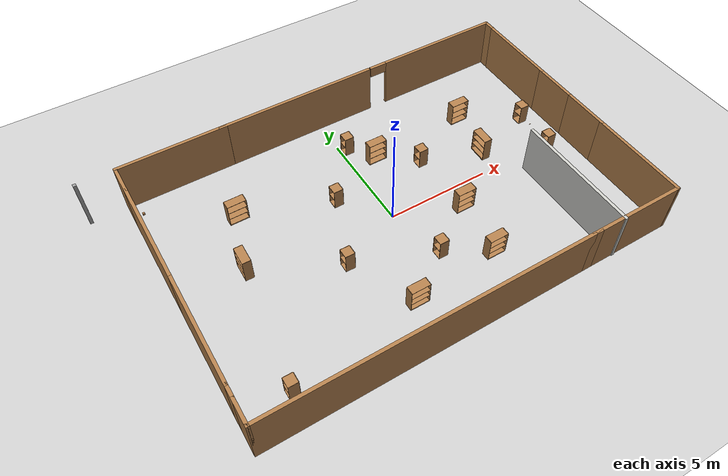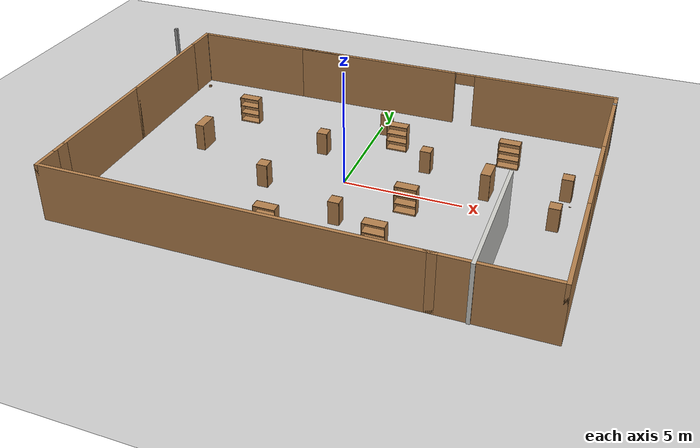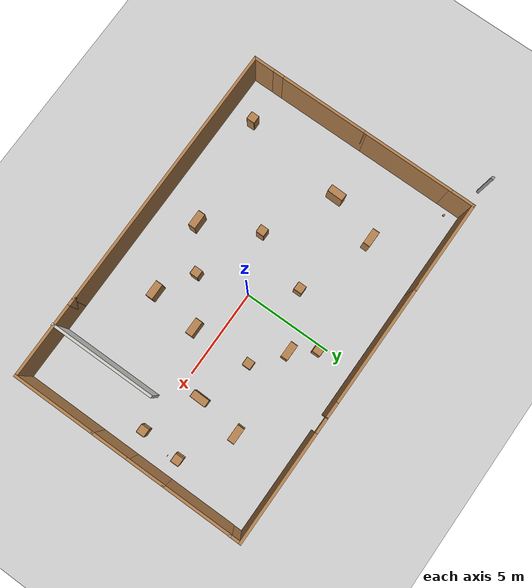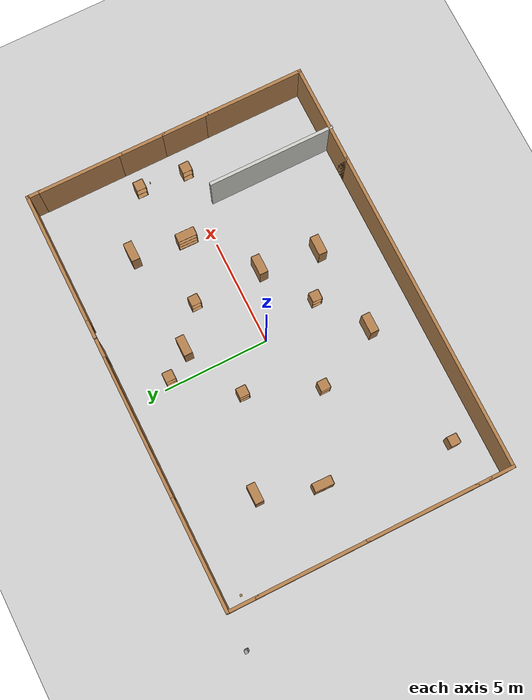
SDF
<sdf version="1.7">
 <world name="default">
  <light name="sun" type="directional">
   <pose>0 0 10 0 -0 0</pose>
   <diffuse>0.8 0.8 0.8 1</diffuse>
   <specular>0.2 0.2 0.2 1</specular>
   <attenuation>
    <range>1000</range>
    <constant>0.9</constant>
    <linear>0.01</linear>
    <quadratic>0.001</quadratic>
   </attenuation>
   <direction>-0.5 0.1 -0.9</direction>
   <spot><inner_angle>0</inner_angle><outer_angle>0</outer_angle><falloff>0</falloff></spot>
  </light>
  <model name="ground_plane">
   <static>1</static>
   <link name="link">
    <collision name="collision">
     <geometry><plane><normal>0 0 1</normal><size>100 100</size></plane></geometry>
     <surface><friction><ode><mu>100</mu><mu2>50</mu2></ode></friction></surface>
    </collision>
    <visual name="visual">
     <cast_shadows>0</cast_shadows>
     <geometry><plane><normal>0 0 1</normal><size>100 100</size></plane></geometry>
     <material>
      <script><uri>file://media/materials/scripts/gazebo.material</uri><name>Gazebo/Grey</name></script>
     </material>
    </visual>
   </link>
  </model>
  <gravity>0 0 -9.8</gravity>
  <magnetic_field>6e-06 2.3e-05 -4.2e-05</magnetic_field>
  <atmosphere type="adiabatic"/>
  <physics type="ode">
   <max_step_size>0.001</max_step_size>
   <real_time_factor>1</real_time_factor>
   <real_time_update_rate>1000</real_time_update_rate>
  </physics>
  <scene><ambient>0.4 0.4 0.4 1</ambient><background>0.7 0.7 0.7 1</background><shadows>1</shadows></scene>
  <audio><device>default</device></audio>
  <spherical_coordinates>
   <surface_model>EARTH_WGS84</surface_model>
   <latitude_deg>0</latitude_deg>
   <longitude_deg>0</longitude_deg>
   <elevation>0</elevation>
   <heading_deg>0</heading_deg>
  </spherical_coordinates>
  <model name="new1">
   <pose>-0.837793 0.046142 0 0 -0 0</pose>
   <link name="Wall_0">
    <collision name="Wall_0_Collision">
     <geometry><box><size>5.25 0.15 2.5</size></box></geometry>
     <pose>0 0 1.25 0 -0 0</pose>
    </collision>
    <visual name="Wall_0_Visual">
     <pose>0 0 1.25 0 -0 0</pose>
     <geometry><box><size>5.25 0.15 2.5</size></box></geometry>
     <material>
      <script><uri>file://media/materials/scripts/gazebo.material</uri><name>Gazebo/Wood</name></script>
      <ambient>1 1 1 1</ambient>
     </material>
     <meta><layer>0</layer></meta>
    </visual>
    <pose>-8.985 -2.355 0 0 -0 -1.5708</pose>
   </link>
   <link name="Wall_12">
    <collision name="Wall_12_Collision">
     <geometry><box><size>4.75 0.15 2.5</size></box></geometry>
     <pose>0 0 1.25 0 -0 0</pose>
    </collision>
    <visual name="Wall_12_Visual">
     <pose>0 0 1.25 0 -0 0</pose>
     <geometry><box><size>4.75 0.15 2.5</size></box></geometry>
     <material>
      <script><uri>file://media/materials/scripts/gazebo.material</uri><name>Gazebo/Wood</name></script>
      <ambient>1 1 1 1</ambient>
     </material>
     <meta><layer>0</layer></meta>
    </visual>
    <pose>10.715 -4.305 0 0 -0 1.5708</pose>
   </link>
   <link name="Wall_14">
    <collision name="Wall_14_Collision">
     <geometry><box><size>2.25 0.15 2.5</size></box></geometry>
     <pose>0 0 1.25 0 -0 0</pose>
    </collision>
    <visual name="Wall_14_Visual">
     <pose>0 0 1.25 0 -0 0</pose>
     <geometry><box><size>2.25 0.15 2.5</size></box></geometry>
     <material>
      <script><uri>file://media/materials/scripts/gazebo.material</uri><name>Gazebo/Wood</name></script>
      <ambient>1 1 1 1</ambient>
     </material>
     <meta><layer>0</layer></meta>
    </visual>
    <pose>10.715 -0.955 0 0 -0 1.5708</pose>
   </link>
   <link name="Wall_16">
    <collision name="Wall_16_Collision">
     <geometry><box><size>2.25 0.15 2.5</size></box></geometry>
     <pose>0 0 1.25 0 -0 0</pose>
    </collision>
    <visual name="Wall_16_Visual">
     <pose>0 0 1.25 0 -0 0</pose>
     <geometry><box><size>2.25 0.15 2.5</size></box></geometry>
     <material>
      <script><uri>file://media/materials/scripts/gazebo.material</uri><name>Gazebo/Wood</name></script>
      <ambient>1 1 1 1</ambient>
     </material>
     <meta><layer>0</layer></meta>
    </visual>
    <pose>10.715 1.145 0 0 -0 1.5708</pose>
   </link>
   <link name="Wall_19">
    <collision name="Wall_19_Collision">
     <geometry><box><size>4 0.15 2.5</size></box></geometry>
     <pose>0 0 1.25 0 -0 0</pose>
    </collision>
    <visual name="Wall_19_Visual">
     <pose>0 0 1.25 0 -0 0</pose>
     <geometry><box><size>4 0.15 2.5</size></box></geometry>
     <material>
      <script><uri>file://media/materials/scripts/gazebo.material</uri><name>Gazebo/Wood</name></script>
      <ambient>1 1 1 1</ambient>
     </material>
     <meta><layer>0</layer></meta>
    </visual>
    <pose>10.715 4.12 0 0 -0 1.5708</pose>
   </link>
   <link name="Wall_2">
    <collision name="Wall_2_Collision">
     <geometry><box><size>0.75 0.15 2.5</size></box></geometry>
     <pose>0 0 1.25 0 -0 0</pose>
    </collision>
    <visual name="Wall_2_Visual">
     <pose>0 0 1.25 0 -0 0</pose>
     <geometry><box><size>0.75 0.15 2.5</size></box></geometry>
     <material>
      <script><uri>file://media/materials/scripts/gazebo.material</uri><name>Gazebo/Wood</name></script>
      <ambient>1 1 1 1</ambient>
     </material>
     <meta><layer>0</layer></meta>
    </visual>
    <pose>-8.985 -5.205 0 0 -0 -1.5708</pose>
   </link>
   <link name="Wall_20">
    <collision name="Wall_20_Collision">
     <geometry><box><size>0.16 0.15 2.5</size></box></geometry>
     <pose>0 0 1.25 0 -0 0</pose>
    </collision>
    <visual name="Wall_20_Visual">
     <pose>0 0 1.25 0 -0 0</pose>
     <geometry><box><size>0.16 0.15 2.5</size></box></geometry>
     <material>
      <script><uri>file://media/materials/scripts/gazebo.material</uri><name>Gazebo/Grey</name></script>
      <ambient>1 1 1 1</ambient>
     </material>
     <meta><layer>0</layer></meta>
    </visual>
    <pose>10.72 6.045 0 0 -0 0</pose>
   </link>
   <link name="Wall_21">
    <collision name="Wall_21_Collision">
     <geometry><box><size>0.75 0.15 2.5</size></box></geometry>
     <pose>0 0 1.25 0 -0 0</pose>
    </collision>
    <visual name="Wall_21_Visual">
     <pose>0 0 1.25 0 -0 0</pose>
     <geometry><box><size>0.75 0.15 2.5</size></box></geometry>
     <material>
      <script><uri>file://media/materials/scripts/gazebo.material</uri><name>Gazebo/Wood</name></script>
      <ambient>1 1 1 1</ambient>
     </material>
     <meta><layer>0</layer></meta>
    </visual>
    <pose>10.725 6.345 0 0 -0 1.5708</pose>
   </link>
   <link name="Wall_22">
    <pose>3.3 6.645 0 0 -0 3.14159</pose>
    <visual name="Wall_22_Visual_0">
     <pose>-4.3875 0 1.25 0 -0 0</pose>
     <geometry><box><size>6.225 0.15 2.5</size></box></geometry>
     <material>
      <script><uri>file://media/materials/scripts/gazebo.material</uri><name>Gazebo/Wood</name></script>
      <ambient>1 1 1 1</ambient>
     </material>
     <meta><layer>0</layer></meta>
    </visual>
    <collision name="Wall_22_Collision_0">
     <geometry><box><size>6.225 0.15 2.5</size></box></geometry>
     <pose>-4.3875 0 1.25 0 -0 0</pose>
    </collision>
    <visual name="Wall_22_Visual_1">
     <pose>3.5625 0 1.25 0 -0 0</pose>
     <geometry><box><size>7.875 0.15 2.5</size></box></geometry>
     <material>
      <script><uri>file://media/materials/scripts/gazebo.material</uri><name>Gazebo/Wood</name></script>
      <ambient>1 1 1 1</ambient>
     </material>
     <meta><layer>0</layer></meta>
    </visual>
    <collision name="Wall_22_Collision_1">
     <geometry><box><size>7.875 0.15 2.5</size></box></geometry>
     <pose>3.5625 0 1.25 0 -0 0</pose>
    </collision>
    <visual name="Wall_22_Visual_2">
     <pose>3.9925 0 1.25 0 -0 0</pose>
     <geometry><box><size>7.015 0.15 2.5</size></box></geometry>
     <material>
      <script><uri>file://media/materials/scripts/gazebo.material</uri><name>Gazebo/Wood</name></script>
      <ambient>1 1 1 1</ambient>
     </material>
     <meta><layer>0</layer></meta>
    </visual>
    <collision name="Wall_22_Collision_2">
     <geometry><box><size>7.015 0.15 2.5</size></box></geometry>
     <pose>3.9925 0 1.25 0 -0 0</pose>
    </collision>
    <visual name="Wall_22_Visual_3">
     <pose>-0.845 0 2.25 0 -0 0</pose>
     <geometry><box><size>0.86 0.15 0.5</size></box></geometry>
     <material>
      <script><uri>file://media/materials/scripts/gazebo.material</uri><name>Gazebo/Wood</name></script>
      <ambient>1 1 1 1</ambient>
     </material>
     <meta><layer>0</layer></meta>
    </visual>
    <collision name="Wall_22_Collision_3">
     <geometry><box><size>0.86 0.15 0.5</size></box></geometry>
     <pose>-0.845 0 2.25 0 -0 0</pose>
    </collision>
   </link>
   <link name="Wall_25">
    <collision name="Wall_25_Collision">
     <geometry><box><size>0.15 0.15 2.5</size></box></geometry>
     <pose>0 0 1.25 0 -0 0</pose>
    </collision>
    <visual name="Wall_25_Visual">
     <pose>0 0 1.25 0 -0 0</pose>
     <geometry><box><size>0.15 0.15 2.5</size></box></geometry>
     <material>
      <script><uri>file://media/materials/scripts/gazebo.material</uri><name>Gazebo/Grey</name></script>
      <ambient>1 1 1 1</ambient>
     </material>
     <meta><layer>0</layer></meta>
    </visual>
    <pose>-10.725 6.645 0 0 -0 0</pose>
   </link>
   <link name="Wall_27">
    <collision name="Wall_27_Collision">
     <geometry><box><size>5.25 0.15 2.5</size></box></geometry>
     <pose>0 0 1.25 0 -0 0</pose>
    </collision>
    <visual name="Wall_27_Visual">
     <pose>0 0 1.25 0 -0 0</pose>
     <geometry><box><size>5.25 0.15 2.5</size></box></geometry>
     <material>
      <script><uri>file://media/materials/scripts/gazebo.material</uri><name>Gazebo/Wood</name></script>
      <ambient>1 1 1 1</ambient>
     </material>
     <meta><layer>0</layer></meta>
    </visual>
    <pose>-8.985 2.745 0 0 -0 1.5708</pose>
   </link>
   <link name="Wall_3">
    <collision name="Wall_3_Collision">
     <geometry><box><size>1.25 0.15 2.5</size></box></geometry>
     <pose>0 0 1.25 0 -0 0</pose>
    </collision>
    <visual name="Wall_3_Visual">
     <pose>0 0 1.25 0 -0 0</pose>
     <geometry><box><size>1.25 0.15 2.5</size></box></geometry>
     <material>
      <script><uri>file://media/materials/scripts/gazebo.material</uri><name>Gazebo/Wood</name></script>
      <ambient>1 1 1 1</ambient>
     </material>
     <meta><layer>0</layer></meta>
    </visual>
    <pose>-8.985 -6.055 0 0 -0 -1.5708</pose>
   </link>
   <link name="Wall_32">
    <collision name="Wall_32_Collision">
     <geometry><box><size>1.5 0.15 2.5</size></box></geometry>
     <pose>0 0 1.25 0 -0 0</pose>
    </collision>
    <visual name="Wall_32_Visual">
     <pose>0 0 1.25 0 -0 0</pose>
     <geometry><box><size>1.5 0.15 2.5</size></box></geometry>
     <material>
      <script><uri>file://media/materials/scripts/gazebo.material</uri><name>Gazebo/Wood</name></script>
      <ambient>1 1 1 1</ambient>
     </material>
     <meta><layer>0</layer></meta>
    </visual>
    <pose>-8.985 5.97 0 0 -0 1.5708</pose>
   </link>
   <link name="Wall_33">
    <collision name="Wall_33_Collision">
     <geometry><box><size>0.16 0.15 2.5</size></box></geometry>
     <pose>0 0 1.25 0 -0 0</pose>
    </collision>
    <visual name="Wall_33_Visual">
     <pose>0 0 1.25 0 -0 0</pose>
     <geometry><box><size>0.16 0.15 2.5</size></box></geometry>
     <material>
      <script><uri>file://media/materials/scripts/gazebo.material</uri><name>Gazebo/Grey</name></script>
      <ambient>1 1 1 1</ambient>
     </material>
     <meta><layer>0</layer></meta>
    </visual>
    <pose>-8.98 6.645 0 0 -0 0</pose>
   </link>
   <link name="Wall_37">
    <collision name="Wall_37_Collision">
     <geometry><box><size>5.25 0.15 2.5</size></box></geometry>
     <pose>0 0 1.25 0 -0 0</pose>
    </collision>
    <visual name="Wall_37_Visual">
     <pose>0 0 1.25 0 -0 0</pose>
     <geometry><box><size>5.25 0.15 2.5</size></box></geometry>
     <material>
      <script><uri>file://media/materials/scripts/gazebo.material</uri><name>Gazebo/Wood</name></script>
      <ambient>1 1 1 1</ambient>
     </material>
     <meta><layer>0</layer></meta>
    </visual>
    <pose>-6.435 6.645 0 0 -0 0</pose>
   </link>
   <link name="Wall_4">
    <collision name="Wall_4_Collision">
     <geometry><box><size>15.25 0.15 2.5</size></box></geometry>
     <pose>0 0 1.25 0 -0 0</pose>
    </collision>
    <visual name="Wall_4_Visual">
     <pose>0 0 1.25 0 -0 0</pose>
     <geometry><box><size>15.25 0.15 2.5</size></box></geometry>
     <material>
      <script><uri>file://media/materials/scripts/gazebo.material</uri><name>Gazebo/Wood</name></script>
      <ambient>1 1 1 1</ambient>
     </material>
     <meta><layer>0</layer></meta>
    </visual>
    <pose>-1.435 -6.605 0 0 -0 0</pose>
   </link>
   <link name="Wall_44">
    <collision name="Wall_44_Collision">
     <geometry><box><size>6 0.15 2.5</size></box></geometry>
     <pose>0 0 1.25 0 -0 0</pose>
    </collision>
    <visual name="Wall_44_Visual">
     <pose>0 0 1.25 0 -0 0</pose>
     <geometry><box><size>6 0.15 2.5</size></box></geometry>
     <material>
      <script><uri>file://media/materials/scripts/gazebo.material</uri><name>Gazebo/CeilingTiled</name></script>
      <ambient>1 1 1 1</ambient>
     </material>
     <meta><layer>0</layer></meta>
    </visual>
    <pose>7.735 -3.72 0 0 -0 1.5708</pose>
   </link>
   <link name="Wall_5">
    <collision name="Wall_5_Collision">
     <geometry><box><size>0.5 0.15 2.5</size></box></geometry>
     <pose>0 0 1.25 0 -0 0</pose>
    </collision>
    <visual name="Wall_5_Visual">
     <pose>0 0 1.25 0 -0 0</pose>
     <geometry><box><size>0.5 0.15 2.5</size></box></geometry>
     <material>
      <script><uri>file://media/materials/scripts/gazebo.material</uri><name>Gazebo/Wood</name></script>
      <ambient>1 1 1 1</ambient>
     </material>
     <meta><layer>0</layer></meta>
    </visual>
    <pose>6.29 -6.605 0 0 -0 0</pose>
   </link>
   <link name="Wall_7">
    <collision name="Wall_7_Collision">
     <geometry><box><size>4.75 0.15 2.5</size></box></geometry>
     <pose>0 0 1.25 0 -0 0</pose>
    </collision>
    <visual name="Wall_7_Visual">
     <pose>0 0 1.25 0 -0 0</pose>
     <geometry><box><size>4.75 0.15 2.5</size></box></geometry>
     <material>
      <script><uri>file://media/materials/scripts/gazebo.material</uri><name>Gazebo/Wood</name></script>
      <ambient>1 1 1 1</ambient>
     </material>
     <meta><layer>0</layer></meta>
    </visual>
    <pose>8.415 -6.605 0 0 -0 0</pose>
   </link>
   <static>1</static>
  </model>
  <model name="bookshelf">
   <static>1</static>
   <link name="link">
    <inertial><mass>1</mass></inertial>
    <collision name="back">
     <pose>0 0.005 0.6 0 -0 0</pose>
     <geometry><box><size>0.9 0.01 1.2</size></box></geometry>
    </collision>
    <visual name="visual1">
     <pose>0 0.005 0.6 0 -0 0</pose>
     <geometry><box><size>0.9 0.01 1.2</size></box></geometry>
     <material>
      <script><uri>file://media/materials/scripts/gazebo.material</uri><name>Gazebo/Wood</name></script>
     </material>
    </visual>
    <collision name="left_side">
     <pose>0.45 -0.195 0.6 0 -0 0</pose>
     <geometry><box><size>0.02 0.4 1.2</size></box></geometry>
    </collision>
    <visual name="visual2">
     <pose>0.45 -0.195 0.6 0 -0 0</pose>
     <geometry><box><size>0.02 0.4 1.2</size></box></geometry>
     <material>
      <script><uri>file://media/materials/scripts/gazebo.material</uri><name>Gazebo/Wood</name></script>
     </material>
    </visual>
    <collision name="right_side">
     <pose>-0.45 -0.195 0.6 0 -0 0</pose>
     <geometry><box><size>0.02 0.4 1.2</size></box></geometry>
    </collision>
    <visual name="visual3">
     <pose>-0.45 -0.195 0.6 0 -0 0</pose>
     <geometry><box><size>0.02 0.4 1.2</size></box></geometry>
     <material>
      <script><uri>file://media/materials/scripts/gazebo.material</uri><name>Gazebo/Wood</name></script>
     </material>
    </visual>
    <collision name="bottom">
     <pose>0 -0.195 0.03 0 -0 0</pose>
     <geometry><box><size>0.88 0.4 0.06</size></box></geometry>
    </collision>
    <visual name="visual4">
     <pose>0 -0.195 0.03 0 -0 0</pose>
     <geometry><box><size>0.88 0.4 0.06</size></box></geometry>
     <material>
      <script><uri>file://media/materials/scripts/gazebo.material</uri><name>Gazebo/Wood</name></script>
     </material>
    </visual>
    <collision name="top">
     <pose>0 -0.195 1.19 0 -0 0</pose>
     <geometry><box><size>0.88 0.4 0.02</size></box></geometry>
    </collision>
    <visual name="visual5">
     <pose>0 -0.195 1.19 0 -0 0</pose>
     <geometry><box><size>0.88 0.4 0.02</size></box></geometry>
     <material>
      <script><uri>file://media/materials/scripts/gazebo.material</uri><name>Gazebo/Wood</name></script>
     </material>
    </visual>
    <collision name="low_shelf">
     <pose>0 -0.195 0.43 0 -0 0</pose>
     <geometry><box><size>0.88 0.4 0.02</size></box></geometry>
    </collision>
    <visual name="visual6">
     <pose>0 -0.195 0.43 0 -0 0</pose>
     <geometry><box><size>0.88 0.4 0.02</size></box></geometry>
     <material>
      <script><uri>file://media/materials/scripts/gazebo.material</uri><name>Gazebo/Wood</name></script>
     </material>
    </visual>
    <collision name="high_shelf">
     <pose>0 -0.195 0.8 0 -0 0</pose>
     <geometry><box><size>0.88 0.4 0.02</size></box></geometry>
    </collision>
    <visual name="visual7">
     <pose>0 -0.195 0.8 0 -0 0</pose>
     <geometry><box><size>0.88 0.4 0.02</size></box></geometry>
     <material>
      <script><uri>file://media/materials/scripts/gazebo.material</uri><name>Gazebo/Wood</name></script>
     </material>
    </visual>
   </link>
   <pose>-5.91249 3.68913 0 0 -0 0</pose>
  </model>
  <model name="bookshelf_clone">
   <static>1</static>
   <link name="link">
    <inertial><mass>1</mass></inertial>
    <collision name="back">
     <pose>0 0.005 0.6 0 -0 0</pose>
     <geometry><box><size>0.9 0.01 1.2</size></box></geometry>
    </collision>
    <visual name="visual1">
     <pose>0 0.005 0.6 0 -0 0</pose>
     <geometry><box><size>0.9 0.01 1.2</size></box></geometry>
     <material>
      <script><uri>file://media/materials/scripts/gazebo.material</uri><name>Gazebo/Wood</name></script>
     </material>
    </visual>
    <collision name="left_side">
     <pose>0.45 -0.195 0.6 0 -0 0</pose>
     <geometry><box><size>0.02 0.4 1.2</size></box></geometry>
    </collision>
    <visual name="visual2">
     <pose>0.45 -0.195 0.6 0 -0 0</pose>
     <geometry><box><size>0.02 0.4 1.2</size></box></geometry>
     <material>
      <script><uri>file://media/materials/scripts/gazebo.material</uri><name>Gazebo/Wood</name></script>
     </material>
    </visual>
    <collision name="right_side">
     <pose>-0.45 -0.195 0.6 0 -0 0</pose>
     <geometry><box><size>0.02 0.4 1.2</size></box></geometry>
    </collision>
    <visual name="visual3">
     <pose>-0.45 -0.195 0.6 0 -0 0</pose>
     <geometry><box><size>0.02 0.4 1.2</size></box></geometry>
     <material>
      <script><uri>file://media/materials/scripts/gazebo.material</uri><name>Gazebo/Wood</name></script>
     </material>
    </visual>
    <collision name="bottom">
     <pose>0 -0.195 0.03 0 -0 0</pose>
     <geometry><box><size>0.88 0.4 0.06</size></box></geometry>
    </collision>
    <visual name="visual4">
     <pose>0 -0.195 0.03 0 -0 0</pose>
     <geometry><box><size>0.88 0.4 0.06</size></box></geometry>
     <material>
      <script><uri>file://media/materials/scripts/gazebo.material</uri><name>Gazebo/Wood</name></script>
     </material>
    </visual>
    <collision name="top">
     <pose>0 -0.195 1.19 0 -0 0</pose>
     <geometry><box><size>0.88 0.4 0.02</size></box></geometry>
    </collision>
    <visual name="visual5">
     <pose>0 -0.195 1.19 0 -0 0</pose>
     <geometry><box><size>0.88 0.4 0.02</size></box></geometry>
     <material>
      <script><uri>file://media/materials/scripts/gazebo.material</uri><name>Gazebo/Wood</name></script>
     </material>
    </visual>
    <collision name="low_shelf">
     <pose>0 -0.195 0.43 0 -0 0</pose>
     <geometry><box><size>0.88 0.4 0.02</size></box></geometry>
    </collision>
    <visual name="visual6">
     <pose>0 -0.195 0.43 0 -0 0</pose>
     <geometry><box><size>0.88 0.4 0.02</size></box></geometry>
     <material>
      <script><uri>file://media/materials/scripts/gazebo.material</uri><name>Gazebo/Wood</name></script>
     </material>
    </visual>
    <collision name="high_shelf">
     <pose>0 -0.195 0.8 0 -0 0</pose>
     <geometry><box><size>0.88 0.4 0.02</size></box></geometry>
    </collision>
    <visual name="visual7">
     <pose>0 -0.195 0.8 0 -0 0</pose>
     <geometry><box><size>0.88 0.4 0.02</size></box></geometry>
     <material>
      <script><uri>file://media/materials/scripts/gazebo.material</uri><name>Gazebo/Wood</name></script>
     </material>
    </visual>
   </link>
   <pose>6.07825 3.82943 0 0 -0 0</pose>
  </model>
  <model name="bookshelf_clone_0">
   <static>1</static>
   <link name="link">
    <inertial><mass>1</mass></inertial>
    <collision name="back">
     <pose>0 0.005 0.6 0 -0 0</pose>
     <geometry><box><size>0.9 0.01 1.2</size></box></geometry>
    </collision>
    <visual name="visual1">
     <pose>0 0.005 0.6 0 -0 0</pose>
     <geometry><box><size>0.9 0.01 1.2</size></box></geometry>
     <material>
      <script><uri>file://media/materials/scripts/gazebo.material</uri><name>Gazebo/Wood</name></script>
     </material>
    </visual>
    <collision name="left_side">
     <pose>0.45 -0.195 0.6 0 -0 0</pose>
     <geometry><box><size>0.02 0.4 1.2</size></box></geometry>
    </collision>
    <visual name="visual2">
     <pose>0.45 -0.195 0.6 0 -0 0</pose>
     <geometry><box><size>0.02 0.4 1.2</size></box></geometry>
     <material>
      <script><uri>file://media/materials/scripts/gazebo.material</uri><name>Gazebo/Wood</name></script>
     </material>
    </visual>
    <collision name="right_side">
     <pose>-0.45 -0.195 0.6 0 -0 0</pose>
     <geometry><box><size>0.02 0.4 1.2</size></box></geometry>
    </collision>
    <visual name="visual3">
     <pose>-0.45 -0.195 0.6 0 -0 0</pose>
     <geometry><box><size>0.02 0.4 1.2</size></box></geometry>
     <material>
      <script><uri>file://media/materials/scripts/gazebo.material</uri><name>Gazebo/Wood</name></script>
     </material>
    </visual>
    <collision name="bottom">
     <pose>0 -0.195 0.03 0 -0 0</pose>
     <geometry><box><size>0.88 0.4 0.06</size></box></geometry>
    </collision>
    <visual name="visual4">
     <pose>0 -0.195 0.03 0 -0 0</pose>
     <geometry><box><size>0.88 0.4 0.06</size></box></geometry>
     <material>
      <script><uri>file://media/materials/scripts/gazebo.material</uri><name>Gazebo/Wood</name></script>
     </material>
    </visual>
    <collision name="top">
     <pose>0 -0.195 1.19 0 -0 0</pose>
     <geometry><box><size>0.88 0.4 0.02</size></box></geometry>
    </collision>
    <visual name="visual5">
     <pose>0 -0.195 1.19 0 -0 0</pose>
     <geometry><box><size>0.88 0.4 0.02</size></box></geometry>
     <material>
      <script><uri>file://media/materials/scripts/gazebo.material</uri><name>Gazebo/Wood</name></script>
     </material>
    </visual>
    <collision name="low_shelf">
     <pose>0 -0.195 0.43 0 -0 0</pose>
     <geometry><box><size>0.88 0.4 0.02</size></box></geometry>
    </collision>
    <visual name="visual6">
     <pose>0 -0.195 0.43 0 -0 0</pose>
     <geometry><box><size>0.88 0.4 0.02</size></box></geometry>
     <material>
      <script><uri>file://media/materials/scripts/gazebo.material</uri><name>Gazebo/Wood</name></script>
     </material>
    </visual>
    <collision name="high_shelf">
     <pose>0 -0.195 0.8 0 -0 0</pose>
     <geometry><box><size>0.88 0.4 0.02</size></box></geometry>
    </collision>
    <visual name="visual7">
     <pose>0 -0.195 0.8 0 -0 0</pose>
     <geometry><box><size>0.88 0.4 0.02</size></box></geometry>
     <material>
      <script><uri>file://media/materials/scripts/gazebo.material</uri><name>Gazebo/Wood</name></script>
     </material>
    </visual>
   </link>
   <pose>2.66451 -3.70633 0 0 -0 0</pose>
  </model>
  <model name="bookshelf_clone_1">
   <static>1</static>
   <link name="link">
    <inertial><mass>1</mass></inertial>
    <collision name="back">
     <pose>0 0.005 0.6 0 -0 0</pose>
     <geometry><box><size>0.9 0.01 1.2</size></box></geometry>
    </collision>
    <visual name="visual1">
     <pose>0 0.005 0.6 0 -0 0</pose>
     <geometry><box><size>0.9 0.01 1.2</size></box></geometry>
     <material>
      <script><uri>file://media/materials/scripts/gazebo.material</uri><name>Gazebo/Wood</name></script>
     </material>
    </visual>
    <collision name="left_side">
     <pose>0.45 -0.195 0.6 0 -0 0</pose>
     <geometry><box><size>0.02 0.4 1.2</size></box></geometry>
    </collision>
    <visual name="visual2">
     <pose>0.45 -0.195 0.6 0 -0 0</pose>
     <geometry><box><size>0.02 0.4 1.2</size></box></geometry>
     <material>
      <script><uri>file://media/materials/scripts/gazebo.material</uri><name>Gazebo/Wood</name></script>
     </material>
    </visual>
    <collision name="right_side">
     <pose>-0.45 -0.195 0.6 0 -0 0</pose>
     <geometry><box><size>0.02 0.4 1.2</size></box></geometry>
    </collision>
    <visual name="visual3">
     <pose>-0.45 -0.195 0.6 0 -0 0</pose>
     <geometry><box><size>0.02 0.4 1.2</size></box></geometry>
     <material>
      <script><uri>file://media/materials/scripts/gazebo.material</uri><name>Gazebo/Wood</name></script>
     </material>
    </visual>
    <collision name="bottom">
     <pose>0 -0.195 0.03 0 -0 0</pose>
     <geometry><box><size>0.88 0.4 0.06</size></box></geometry>
    </collision>
    <visual name="visual4">
     <pose>0 -0.195 0.03 0 -0 0</pose>
     <geometry><box><size>0.88 0.4 0.06</size></box></geometry>
     <material>
      <script><uri>file://media/materials/scripts/gazebo.material</uri><name>Gazebo/Wood</name></script>
     </material>
    </visual>
    <collision name="top">
     <pose>0 -0.195 1.19 0 -0 0</pose>
     <geometry><box><size>0.88 0.4 0.02</size></box></geometry>
    </collision>
    <visual name="visual5">
     <pose>0 -0.195 1.19 0 -0 0</pose>
     <geometry><box><size>0.88 0.4 0.02</size></box></geometry>
     <material>
      <script><uri>file://media/materials/scripts/gazebo.material</uri><name>Gazebo/Wood</name></script>
     </material>
    </visual>
    <collision name="low_shelf">
     <pose>0 -0.195 0.43 0 -0 0</pose>
     <geometry><box><size>0.88 0.4 0.02</size></box></geometry>
    </collision>
    <visual name="visual6">
     <pose>0 -0.195 0.43 0 -0 0</pose>
     <geometry><box><size>0.88 0.4 0.02</size></box></geometry>
     <material>
      <script><uri>file://media/materials/scripts/gazebo.material</uri><name>Gazebo/Wood</name></script>
     </material>
    </visual>
    <collision name="high_shelf">
     <pose>0 -0.195 0.8 0 -0 0</pose>
     <geometry><box><size>0.88 0.4 0.02</size></box></geometry>
    </collision>
    <visual name="visual7">
     <pose>0 -0.195 0.8 0 -0 0</pose>
     <geometry><box><size>0.88 0.4 0.02</size></box></geometry>
     <material>
      <script><uri>file://media/materials/scripts/gazebo.material</uri><name>Gazebo/Wood</name></script>
     </material>
    </visual>
   </link>
   <pose>-1.5109 -4.1059 0 0 -0 0</pose>
  </model>
  <model name="cabinet">
   <static>1</static>
   <link name="cabinet_bottom_plate">
    <inertial>
     <pose>0 0 -1 0 -0 0</pose>
     <inertia><ixx>2.05</ixx><ixy>0</ixy><ixz>0</ixz><iyy>2.05</iyy><iyz>0</iyz><izz>2.05</izz></inertia>
     <mass>25</mass>
    </inertial>
    <collision name="cabinet_bottom_plate_geom">
     <pose>0 0 0.01 0 -0 0</pose>
     <geometry><box><size>0.45 0.45 0.02</size></box></geometry>
    </collision>
    <visual name="cabinet_bottom_plate_geom_visual">
     <pose>0 0 0.01 0 -0 0</pose>
     <geometry><box><size>0.45 0.45 0.02</size></box></geometry>
     <material>
      <script><uri>file://media/materials/scripts/gazebo.material</uri><name>Gazebo/Wood</name></script>
     </material>
    </visual>
    <collision name="cabinet_bottom_plate_geom_cabinet_back_plate">
     <pose>0.235 0 0.51 0 -0 0</pose>
     <geometry><box><size>0.02 0.45 1.02</size></box></geometry>
    </collision>
    <visual name="cabinet_bottom_plate_geom_cabinet_back_plate_visual">
     <pose>0.235 0 0.51 0 -0 0</pose>
     <geometry><box><size>0.02 0.45 1.02</size></box></geometry>
     <material>
      <script><uri>file://media/materials/scripts/gazebo.material</uri><name>Gazebo/Wood</name></script>
     </material>
    </visual>
    <collision name="cabinet_bottom_plate_geom_cabinet_left_plate">
     <pose>0 0.235 0.51 0 -0 0</pose>
     <geometry><box><size>0.45 0.02 1.02</size></box></geometry>
    </collision>
    <visual name="cabinet_bottom_plate_geom_cabinet_left_plate_visual">
     <pose>0 0.235 0.51 0 -0 0</pose>
     <geometry><box><size>0.45 0.02 1.02</size></box></geometry>
     <material>
      <script><uri>file://media/materials/scripts/gazebo.material</uri><name>Gazebo/Wood</name></script>
     </material>
    </visual>
    <collision name="cabinet_bottom_plate_geom_cabinet_middle_plate">
     <pose>0 0 0.51 0 -0 0</pose>
     <geometry><box><size>0.45 0.45 0.02</size></box></geometry>
    </collision>
    <visual name="cabinet_bottom_plate_geom_cabinet_middle_plate_visual">
     <pose>0 0 0.51 0 -0 0</pose>
     <geometry><box><size>0.45 0.45 0.02</size></box></geometry>
     <material>
      <script><uri>file://media/materials/scripts/gazebo.material</uri><name>Gazebo/Wood</name></script>
     </material>
    </visual>
    <collision name="cabinet_bottom_plate_geom_cabinet_right_plate">
     <pose>0 -0.235 0.51 0 -0 0</pose>
     <geometry><box><size>0.45 0.02 1.02</size></box></geometry>
    </collision>
    <visual name="cabinet_bottom_plate_geom_cabinet_right_plate_visual">
     <pose>0 -0.235 0.51 0 -0 0</pose>
     <geometry><box><size>0.45 0.02 1.02</size></box></geometry>
     <material>
      <script><uri>file://media/materials/scripts/gazebo.material</uri><name>Gazebo/Wood</name></script>
     </material>
    </visual>
    <collision name="cabinet_bottom_plate_geom_cabinet_top_plate">
     <pose>0 0 1.01 0 -0 0</pose>
     <geometry><box><size>0.45 0.45 0.02</size></box></geometry>
    </collision>
    <visual name="cabinet_bottom_plate_geom_cabinet_top_plate_visual">
     <pose>0 0 1.01 0 -0 0</pose>
     <geometry><box><size>0.45 0.45 0.02</size></box></geometry>
     <material>
      <script><uri>file://media/materials/scripts/gazebo.material</uri><name>Gazebo/Wood</name></script>
     </material>
    </visual>
   </link>
   <pose>-3.02863 -1.26093 0 0 -0 0</pose>
  </model>
  <model name="cabinet_clone">
   <static>1</static>
   <link name="cabinet_bottom_plate">
    <inertial>
     <pose>0 0 -1 0 -0 0</pose>
     <inertia><ixx>2.05</ixx><ixy>0</ixy><ixz>0</ixz><iyy>2.05</iyy><iyz>0</iyz><izz>2.05</izz></inertia>
     <mass>25</mass>
    </inertial>
    <collision name="cabinet_bottom_plate_geom">
     <pose>0 0 0.01 0 -0 0</pose>
     <geometry><box><size>0.45 0.45 0.02</size></box></geometry>
    </collision>
    <visual name="cabinet_bottom_plate_geom_visual">
     <pose>0 0 0.01 0 -0 0</pose>
     <geometry><box><size>0.45 0.45 0.02</size></box></geometry>
     <material>
      <script><uri>file://media/materials/scripts/gazebo.material</uri><name>Gazebo/Wood</name></script>
     </material>
    </visual>
    <collision name="cabinet_bottom_plate_geom_cabinet_back_plate">
     <pose>0.235 0 0.51 0 -0 0</pose>
     <geometry><box><size>0.02 0.45 1.02</size></box></geometry>
    </collision>
    <visual name="cabinet_bottom_plate_geom_cabinet_back_plate_visual">
     <pose>0.235 0 0.51 0 -0 0</pose>
     <geometry><box><size>0.02 0.45 1.02</size></box></geometry>
     <material>
      <script><uri>file://media/materials/scripts/gazebo.material</uri><name>Gazebo/Wood</name></script>
     </material>
    </visual>
    <collision name="cabinet_bottom_plate_geom_cabinet_left_plate">
     <pose>0 0.235 0.51 0 -0 0</pose>
     <geometry><box><size>0.45 0.02 1.02</size></box></geometry>
    </collision>
    <visual name="cabinet_bottom_plate_geom_cabinet_left_plate_visual">
     <pose>0 0.235 0.51 0 -0 0</pose>
     <geometry><box><size>0.45 0.02 1.02</size></box></geometry>
     <material>
      <script><uri>file://media/materials/scripts/gazebo.material</uri><name>Gazebo/Wood</name></script>
     </material>
    </visual>
    <collision name="cabinet_bottom_plate_geom_cabinet_middle_plate">
     <pose>0 0 0.51 0 -0 0</pose>
     <geometry><box><size>0.45 0.45 0.02</size></box></geometry>
    </collision>
    <visual name="cabinet_bottom_plate_geom_cabinet_middle_plate_visual">
     <pose>0 0 0.51 0 -0 0</pose>
     <geometry><box><size>0.45 0.45 0.02</size></box></geometry>
     <material>
      <script><uri>file://media/materials/scripts/gazebo.material</uri><name>Gazebo/Wood</name></script>
     </material>
    </visual>
    <collision name="cabinet_bottom_plate_geom_cabinet_right_plate">
     <pose>0 -0.235 0.51 0 -0 0</pose>
     <geometry><box><size>0.45 0.02 1.02</size></box></geometry>
    </collision>
    <visual name="cabinet_bottom_plate_geom_cabinet_right_plate_visual">
     <pose>0 -0.235 0.51 0 -0 0</pose>
     <geometry><box><size>0.45 0.02 1.02</size></box></geometry>
     <material>
      <script><uri>file://media/materials/scripts/gazebo.material</uri><name>Gazebo/Wood</name></script>
     </material>
    </visual>
    <collision name="cabinet_bottom_plate_geom_cabinet_top_plate">
     <pose>0 0 1.01 0 -0 0</pose>
     <geometry><box><size>0.45 0.45 0.02</size></box></geometry>
    </collision>
    <visual name="cabinet_bottom_plate_geom_cabinet_top_plate_visual">
     <pose>0 0 1.01 0 -0 0</pose>
     <geometry><box><size>0.45 0.45 0.02</size></box></geometry>
     <material>
      <script><uri>file://media/materials/scripts/gazebo.material</uri><name>Gazebo/Wood</name></script>
     </material>
    </visual>
   </link>
   <pose>2.88557 2.11022 0 0 -0 0</pose>
  </model>
  <model name="cabinet_clone_0">
   <static>1</static>
   <link name="cabinet_bottom_plate">
    <inertial>
     <pose>0 0 -1 0 -0 0</pose>
     <inertia><ixx>2.05</ixx><ixy>0</ixy><ixz>0</ixz><iyy>2.05</iyy><iyz>0</iyz><izz>2.05</izz></inertia>
     <mass>25</mass>
    </inertial>
    <collision name="cabinet_bottom_plate_geom">
     <pose>0 0 0.01 0 -0 0</pose>
     <geometry><box><size>0.45 0.45 0.02</size></box></geometry>
    </collision>
    <visual name="cabinet_bottom_plate_geom_visual">
     <pose>0 0 0.01 0 -0 0</pose>
     <geometry><box><size>0.45 0.45 0.02</size></box></geometry>
     <material>
      <script><uri>file://media/materials/scripts/gazebo.material</uri><name>Gazebo/Wood</name></script>
     </material>
    </visual>
    <collision name="cabinet_bottom_plate_geom_cabinet_back_plate">
     <pose>0.235 0 0.51 0 -0 0</pose>
     <geometry><box><size>0.02 0.45 1.02</size></box></geometry>
    </collision>
    <visual name="cabinet_bottom_plate_geom_cabinet_back_plate_visual">
     <pose>0.235 0 0.51 0 -0 0</pose>
     <geometry><box><size>0.02 0.45 1.02</size></box></geometry>
     <material>
      <script><uri>file://media/materials/scripts/gazebo.material</uri><name>Gazebo/Wood</name></script>
     </material>
    </visual>
    <collision name="cabinet_bottom_plate_geom_cabinet_left_plate">
     <pose>0 0.235 0.51 0 -0 0</pose>
     <geometry><box><size>0.45 0.02 1.02</size></box></geometry>
    </collision>
    <visual name="cabinet_bottom_plate_geom_cabinet_left_plate_visual">
     <pose>0 0.235 0.51 0 -0 0</pose>
     <geometry><box><size>0.45 0.02 1.02</size></box></geometry>
     <material>
      <script><uri>file://media/materials/scripts/gazebo.material</uri><name>Gazebo/Wood</name></script>
     </material>
    </visual>
    <collision name="cabinet_bottom_plate_geom_cabinet_middle_plate">
     <pose>0 0 0.51 0 -0 0</pose>
     <geometry><box><size>0.45 0.45 0.02</size></box></geometry>
    </collision>
    <visual name="cabinet_bottom_plate_geom_cabinet_middle_plate_visual">
     <pose>0 0 0.51 0 -0 0</pose>
     <geometry><box><size>0.45 0.45 0.02</size></box></geometry>
     <material>
      <script><uri>file://media/materials/scripts/gazebo.material</uri><name>Gazebo/Wood</name></script>
     </material>
    </visual>
    <collision name="cabinet_bottom_plate_geom_cabinet_right_plate">
     <pose>0 -0.235 0.51 0 -0 0</pose>
     <geometry><box><size>0.45 0.02 1.02</size></box></geometry>
    </collision>
    <visual name="cabinet_bottom_plate_geom_cabinet_right_plate_visual">
     <pose>0 -0.235 0.51 0 -0 0</pose>
     <geometry><box><size>0.45 0.02 1.02</size></box></geometry>
     <material>
      <script><uri>file://media/materials/scripts/gazebo.material</uri><name>Gazebo/Wood</name></script>
     </material>
    </visual>
    <collision name="cabinet_bottom_plate_geom_cabinet_top_plate">
     <pose>0 0 1.01 0 -0 0</pose>
     <geometry><box><size>0.45 0.45 0.02</size></box></geometry>
    </collision>
    <visual name="cabinet_bottom_plate_geom_cabinet_top_plate_visual">
     <pose>0 0 1.01 0 -0 0</pose>
     <geometry><box><size>0.45 0.45 0.02</size></box></geometry>
     <material>
      <script><uri>file://media/materials/scripts/gazebo.material</uri><name>Gazebo/Wood</name></script>
     </material>
    </visual>
   </link>
   <pose>0.677816 -2.7426 0 0 -0 0</pose>
  </model>
  <model name="cabinet_clone_clone">
   <static>1</static>
   <link name="cabinet_bottom_plate">
    <inertial>
     <pose>0 0 -1 0 -0 0</pose>
     <inertia><ixx>2.05</ixx><ixy>0</ixy><ixz>0</ixz><iyy>2.05</iyy><iyz>0</iyz><izz>2.05</izz></inertia>
     <mass>25</mass>
    </inertial>
    <collision name="cabinet_bottom_plate_geom">
     <pose>0 0 0.01 0 -0 0</pose>
     <geometry><box><size>0.45 0.45 0.02</size></box></geometry>
    </collision>
    <visual name="cabinet_bottom_plate_geom_visual">
     <pose>0 0 0.01 0 -0 0</pose>
     <geometry><box><size>0.45 0.45 0.02</size></box></geometry>
     <material>
      <script><uri>file://media/materials/scripts/gazebo.material</uri><name>Gazebo/Wood</name></script>
     </material>
    </visual>
    <collision name="cabinet_bottom_plate_geom_cabinet_back_plate">
     <pose>0.235 0 0.51 0 -0 0</pose>
     <geometry><box><size>0.02 0.45 1.02</size></box></geometry>
    </collision>
    <visual name="cabinet_bottom_plate_geom_cabinet_back_plate_visual">
     <pose>0.235 0 0.51 0 -0 0</pose>
     <geometry><box><size>0.02 0.45 1.02</size></box></geometry>
     <material>
      <script><uri>file://media/materials/scripts/gazebo.material</uri><name>Gazebo/Wood</name></script>
     </material>
    </visual>
    <collision name="cabinet_bottom_plate_geom_cabinet_left_plate">
     <pose>0 0.235 0.51 0 -0 0</pose>
     <geometry><box><size>0.45 0.02 1.02</size></box></geometry>
    </collision>
    <visual name="cabinet_bottom_plate_geom_cabinet_left_plate_visual">
     <pose>0 0.235 0.51 0 -0 0</pose>
     <geometry><box><size>0.45 0.02 1.02</size></box></geometry>
     <material>
      <script><uri>file://media/materials/scripts/gazebo.material</uri><name>Gazebo/Wood</name></script>
     </material>
    </visual>
    <collision name="cabinet_bottom_plate_geom_cabinet_middle_plate">
     <pose>0 0 0.51 0 -0 0</pose>
     <geometry><box><size>0.45 0.45 0.02</size></box></geometry>
    </collision>
    <visual name="cabinet_bottom_plate_geom_cabinet_middle_plate_visual">
     <pose>0 0 0.51 0 -0 0</pose>
     <geometry><box><size>0.45 0.45 0.02</size></box></geometry>
     <material>
      <script><uri>file://media/materials/scripts/gazebo.material</uri><name>Gazebo/Wood</name></script>
     </material>
    </visual>
    <collision name="cabinet_bottom_plate_geom_cabinet_right_plate">
     <pose>0 -0.235 0.51 0 -0 0</pose>
     <geometry><box><size>0.45 0.02 1.02</size></box></geometry>
    </collision>
    <visual name="cabinet_bottom_plate_geom_cabinet_right_plate_visual">
     <pose>0 -0.235 0.51 0 -0 0</pose>
     <geometry><box><size>0.45 0.02 1.02</size></box></geometry>
     <material>
      <script><uri>file://media/materials/scripts/gazebo.material</uri><name>Gazebo/Wood</name></script>
     </material>
    </visual>
    <collision name="cabinet_bottom_plate_geom_cabinet_top_plate">
     <pose>0 0 1.01 0 -0 0</pose>
     <geometry><box><size>0.45 0.45 0.02</size></box></geometry>
    </collision>
    <visual name="cabinet_bottom_plate_geom_cabinet_top_plate_visual">
     <pose>0 0 1.01 0 -0 0</pose>
     <geometry><box><size>0.45 0.45 0.02</size></box></geometry>
     <material>
      <script><uri>file://media/materials/scripts/gazebo.material</uri><name>Gazebo/Wood</name></script>
     </material>
    </visual>
   </link>
   <pose>8.76162 2.00262 0 0 -0 0</pose>
  </model>
  <model name="cabinet_clone_clone_0">
   <static>1</static>
   <link name="cabinet_bottom_plate">
    <inertial>
     <pose>0 0 -1 0 -0 0</pose>
     <inertia><ixx>2.05</ixx><ixy>0</ixy><ixz>0</ixz><iyy>2.05</iyy><iyz>0</iyz><izz>2.05</izz></inertia>
     <mass>25</mass>
    </inertial>
    <collision name="cabinet_bottom_plate_geom">
     <pose>0 0 0.01 0 -0 0</pose>
     <geometry><box><size>0.45 0.45 0.02</size></box></geometry>
    </collision>
    <visual name="cabinet_bottom_plate_geom_visual">
     <pose>0 0 0.01 0 -0 0</pose>
     <geometry><box><size>0.45 0.45 0.02</size></box></geometry>
     <material>
      <script><uri>file://media/materials/scripts/gazebo.material</uri><name>Gazebo/Wood</name></script>
     </material>
    </visual>
    <collision name="cabinet_bottom_plate_geom_cabinet_back_plate">
     <pose>0.235 0 0.51 0 -0 0</pose>
     <geometry><box><size>0.02 0.45 1.02</size></box></geometry>
    </collision>
    <visual name="cabinet_bottom_plate_geom_cabinet_back_plate_visual">
     <pose>0.235 0 0.51 0 -0 0</pose>
     <geometry><box><size>0.02 0.45 1.02</size></box></geometry>
     <material>
      <script><uri>file://media/materials/scripts/gazebo.material</uri><name>Gazebo/Wood</name></script>
     </material>
    </visual>
    <collision name="cabinet_bottom_plate_geom_cabinet_left_plate">
     <pose>0 0.235 0.51 0 -0 0</pose>
     <geometry><box><size>0.45 0.02 1.02</size></box></geometry>
    </collision>
    <visual name="cabinet_bottom_plate_geom_cabinet_left_plate_visual">
     <pose>0 0.235 0.51 0 -0 0</pose>
     <geometry><box><size>0.45 0.02 1.02</size></box></geometry>
     <material>
      <script><uri>file://media/materials/scripts/gazebo.material</uri><name>Gazebo/Wood</name></script>
     </material>
    </visual>
    <collision name="cabinet_bottom_plate_geom_cabinet_middle_plate">
     <pose>0 0 0.51 0 -0 0</pose>
     <geometry><box><size>0.45 0.45 0.02</size></box></geometry>
    </collision>
    <visual name="cabinet_bottom_plate_geom_cabinet_middle_plate_visual">
     <pose>0 0 0.51 0 -0 0</pose>
     <geometry><box><size>0.45 0.45 0.02</size></box></geometry>
     <material>
      <script><uri>file://media/materials/scripts/gazebo.material</uri><name>Gazebo/Wood</name></script>
     </material>
    </visual>
    <collision name="cabinet_bottom_plate_geom_cabinet_right_plate">
     <pose>0 -0.235 0.51 0 -0 0</pose>
     <geometry><box><size>0.45 0.02 1.02</size></box></geometry>
    </collision>
    <visual name="cabinet_bottom_plate_geom_cabinet_right_plate_visual">
     <pose>0 -0.235 0.51 0 -0 0</pose>
     <geometry><box><size>0.45 0.02 1.02</size></box></geometry>
     <material>
      <script><uri>file://media/materials/scripts/gazebo.material</uri><name>Gazebo/Wood</name></script>
     </material>
    </visual>
    <collision name="cabinet_bottom_plate_geom_cabinet_top_plate">
     <pose>0 0 1.01 0 -0 0</pose>
     <geometry><box><size>0.45 0.45 0.02</size></box></geometry>
    </collision>
    <visual name="cabinet_bottom_plate_geom_cabinet_top_plate_visual">
     <pose>0 0 1.01 0 -0 0</pose>
     <geometry><box><size>0.45 0.45 0.02</size></box></geometry>
     <material>
      <script><uri>file://media/materials/scripts/gazebo.material</uri><name>Gazebo/Wood</name></script>
     </material>
    </visual>
   </link>
   <pose>0.315863 4.58278 0 0 -0 0</pose>
  </model>
  <model name="cabinet_clone_1">
   <static>1</static>
   <link name="cabinet_bottom_plate">
    <inertial>
     <pose>0 0 -1 0 -0 0</pose>
     <inertia><ixx>2.05</ixx><ixy>0</ixy><ixz>0</ixz><iyy>2.05</iyy><iyz>0</iyz><izz>2.05</izz></inertia>
     <mass>25</mass>
    </inertial>
    <collision name="cabinet_bottom_plate_geom">
     <pose>0 0 0.01 0 -0 0</pose>
     <geometry><box><size>0.45 0.45 0.02</size></box></geometry>
    </collision>
    <visual name="cabinet_bottom_plate_geom_visual">
     <pose>0 0 0.01 0 -0 0</pose>
     <geometry><box><size>0.45 0.45 0.02</size></box></geometry>
     <material>
      <script><uri>file://media/materials/scripts/gazebo.material</uri><name>Gazebo/Wood</name></script>
     </material>
    </visual>
    <collision name="cabinet_bottom_plate_geom_cabinet_back_plate">
     <pose>0.235 0 0.51 0 -0 0</pose>
     <geometry><box><size>0.02 0.45 1.02</size></box></geometry>
    </collision>
    <visual name="cabinet_bottom_plate_geom_cabinet_back_plate_visual">
     <pose>0.235 0 0.51 0 -0 0</pose>
     <geometry><box><size>0.02 0.45 1.02</size></box></geometry>
     <material>
      <script><uri>file://media/materials/scripts/gazebo.material</uri><name>Gazebo/Wood</name></script>
     </material>
    </visual>
    <collision name="cabinet_bottom_plate_geom_cabinet_left_plate">
     <pose>0 0.235 0.51 0 -0 0</pose>
     <geometry><box><size>0.45 0.02 1.02</size></box></geometry>
    </collision>
    <visual name="cabinet_bottom_plate_geom_cabinet_left_plate_visual">
     <pose>0 0.235 0.51 0 -0 0</pose>
     <geometry><box><size>0.45 0.02 1.02</size></box></geometry>
     <material>
      <script><uri>file://media/materials/scripts/gazebo.material</uri><name>Gazebo/Wood</name></script>
     </material>
    </visual>
    <collision name="cabinet_bottom_plate_geom_cabinet_middle_plate">
     <pose>0 0 0.51 0 -0 0</pose>
     <geometry><box><size>0.45 0.45 0.02</size></box></geometry>
    </collision>
    <visual name="cabinet_bottom_plate_geom_cabinet_middle_plate_visual">
     <pose>0 0 0.51 0 -0 0</pose>
     <geometry><box><size>0.45 0.45 0.02</size></box></geometry>
     <material>
      <script><uri>file://media/materials/scripts/gazebo.material</uri><name>Gazebo/Wood</name></script>
     </material>
    </visual>
    <collision name="cabinet_bottom_plate_geom_cabinet_right_plate">
     <pose>0 -0.235 0.51 0 -0 0</pose>
     <geometry><box><size>0.45 0.02 1.02</size></box></geometry>
    </collision>
    <visual name="cabinet_bottom_plate_geom_cabinet_right_plate_visual">
     <pose>0 -0.235 0.51 0 -0 0</pose>
     <geometry><box><size>0.45 0.02 1.02</size></box></geometry>
     <material>
      <script><uri>file://media/materials/scripts/gazebo.material</uri><name>Gazebo/Wood</name></script>
     </material>
    </visual>
    <collision name="cabinet_bottom_plate_geom_cabinet_top_plate">
     <pose>0 0 1.01 0 -0 0</pose>
     <geometry><box><size>0.45 0.45 0.02</size></box></geometry>
    </collision>
    <visual name="cabinet_bottom_plate_geom_cabinet_top_plate_visual">
     <pose>0 0 1.01 0 -0 0</pose>
     <geometry><box><size>0.45 0.45 0.02</size></box></geometry>
     <material>
      <script><uri>file://media/materials/scripts/gazebo.material</uri><name>Gazebo/Wood</name></script>
     </material>
    </visual>
   </link>
   <pose>-1.7238 2.01899 0 0 -0 0</pose>
  </model>
  <model name="bookshelf_clone_0_clone">
   <static>1</static>
   <link name="link">
    <inertial><mass>1</mass></inertial>
    <collision name="back">
     <pose>0 0.005 0.6 0 -0 0</pose>
     <geometry><box><size>0.9 0.01 1.2</size></box></geometry>
    </collision>
    <visual name="visual1">
     <pose>0 0.005 0.6 0 -0 0</pose>
     <geometry><box><size>0.9 0.01 1.2</size></box></geometry>
     <material>
      <script><uri>file://media/materials/scripts/gazebo.material</uri><name>Gazebo/Wood</name></script>
     </material>
    </visual>
    <collision name="left_side">
     <pose>0.45 -0.195 0.6 0 -0 0</pose>
     <geometry><box><size>0.02 0.4 1.2</size></box></geometry>
    </collision>
    <visual name="visual2">
     <pose>0.45 -0.195 0.6 0 -0 0</pose>
     <geometry><box><size>0.02 0.4 1.2</size></box></geometry>
     <material>
      <script><uri>file://media/materials/scripts/gazebo.material</uri><name>Gazebo/Wood</name></script>
     </material>
    </visual>
    <collision name="right_side">
     <pose>-0.45 -0.195 0.6 0 -0 0</pose>
     <geometry><box><size>0.02 0.4 1.2</size></box></geometry>
    </collision>
    <visual name="visual3">
     <pose>-0.45 -0.195 0.6 0 -0 0</pose>
     <geometry><box><size>0.02 0.4 1.2</size></box></geometry>
     <material>
      <script><uri>file://media/materials/scripts/gazebo.material</uri><name>Gazebo/Wood</name></script>
     </material>
    </visual>
    <collision name="bottom">
     <pose>0 -0.195 0.03 0 -0 0</pose>
     <geometry><box><size>0.88 0.4 0.06</size></box></geometry>
    </collision>
    <visual name="visual4">
     <pose>0 -0.195 0.03 0 -0 0</pose>
     <geometry><box><size>0.88 0.4 0.06</size></box></geometry>
     <material>
      <script><uri>file://media/materials/scripts/gazebo.material</uri><name>Gazebo/Wood</name></script>
     </material>
    </visual>
    <collision name="top">
     <pose>0 -0.195 1.19 0 -0 0</pose>
     <geometry><box><size>0.88 0.4 0.02</size></box></geometry>
    </collision>
    <visual name="visual5">
     <pose>0 -0.195 1.19 0 -0 0</pose>
     <geometry><box><size>0.88 0.4 0.02</size></box></geometry>
     <material>
      <script><uri>file://media/materials/scripts/gazebo.material</uri><name>Gazebo/Wood</name></script>
     </material>
    </visual>
    <collision name="low_shelf">
     <pose>0 -0.195 0.43 0 -0 0</pose>
     <geometry><box><size>0.88 0.4 0.02</size></box></geometry>
    </collision>
    <visual name="visual6">
     <pose>0 -0.195 0.43 0 -0 0</pose>
     <geometry><box><size>0.88 0.4 0.02</size></box></geometry>
     <material>
      <script><uri>file://media/materials/scripts/gazebo.material</uri><name>Gazebo/Wood</name></script>
     </material>
    </visual>
    <collision name="high_shelf">
     <pose>0 -0.195 0.8 0 -0 0</pose>
     <geometry><box><size>0.88 0.4 0.02</size></box></geometry>
    </collision>
    <visual name="visual7">
     <pose>0 -0.195 0.8 0 -0 0</pose>
     <geometry><box><size>0.88 0.4 0.02</size></box></geometry>
     <material>
      <script><uri>file://media/materials/scripts/gazebo.material</uri><name>Gazebo/Wood</name></script>
     </material>
    </visual>
   </link>
   <pose>3.02321 -0.96416 0 0 -0 0</pose>
  </model>
  <model name="cabinet_clone_2">
   <static>1</static>
   <link name="cabinet_bottom_plate">
    <inertial>
     <pose>0 0 -1 0 -0 0</pose>
     <inertia><ixx>2.05</ixx><ixy>0</ixy><ixz>0</ixz><iyy>2.05</iyy><iyz>0</iyz><izz>2.05</izz></inertia>
     <mass>25</mass>
    </inertial>
    <collision name="cabinet_bottom_plate_geom">
     <pose>0 0 0.01 0 -0 0</pose>
     <geometry><box><size>0.45 0.45 0.02</size></box></geometry>
    </collision>
    <visual name="cabinet_bottom_plate_geom_visual">
     <pose>0 0 0.01 0 -0 0</pose>
     <geometry><box><size>0.45 0.45 0.02</size></box></geometry>
     <material>
      <script><uri>file://media/materials/scripts/gazebo.material</uri><name>Gazebo/Wood</name></script>
     </material>
    </visual>
    <collision name="cabinet_bottom_plate_geom_cabinet_back_plate">
     <pose>0.235 0 0.51 0 -0 0</pose>
     <geometry><box><size>0.02 0.45 1.02</size></box></geometry>
    </collision>
    <visual name="cabinet_bottom_plate_geom_cabinet_back_plate_visual">
     <pose>0.235 0 0.51 0 -0 0</pose>
     <geometry><box><size>0.02 0.45 1.02</size></box></geometry>
     <material>
      <script><uri>file://media/materials/scripts/gazebo.material</uri><name>Gazebo/Wood</name></script>
     </material>
    </visual>
    <collision name="cabinet_bottom_plate_geom_cabinet_left_plate">
     <pose>0 0.235 0.51 0 -0 0</pose>
     <geometry><box><size>0.45 0.02 1.02</size></box></geometry>
    </collision>
    <visual name="cabinet_bottom_plate_geom_cabinet_left_plate_visual">
     <pose>0 0.235 0.51 0 -0 0</pose>
     <geometry><box><size>0.45 0.02 1.02</size></box></geometry>
     <material>
      <script><uri>file://media/materials/scripts/gazebo.material</uri><name>Gazebo/Wood</name></script>
     </material>
    </visual>
    <collision name="cabinet_bottom_plate_geom_cabinet_middle_plate">
     <pose>0 0 0.51 0 -0 0</pose>
     <geometry><box><size>0.45 0.45 0.02</size></box></geometry>
    </collision>
    <visual name="cabinet_bottom_plate_geom_cabinet_middle_plate_visual">
     <pose>0 0 0.51 0 -0 0</pose>
     <geometry><box><size>0.45 0.45 0.02</size></box></geometry>
     <material>
      <script><uri>file://media/materials/scripts/gazebo.material</uri><name>Gazebo/Wood</name></script>
     </material>
    </visual>
    <collision name="cabinet_bottom_plate_geom_cabinet_right_plate">
     <pose>0 -0.235 0.51 0 -0 0</pose>
     <geometry><box><size>0.45 0.02 1.02</size></box></geometry>
    </collision>
    <visual name="cabinet_bottom_plate_geom_cabinet_right_plate_visual">
     <pose>0 -0.235 0.51 0 -0 0</pose>
     <geometry><box><size>0.45 0.02 1.02</size></box></geometry>
     <material>
      <script><uri>file://media/materials/scripts/gazebo.material</uri><name>Gazebo/Wood</name></script>
     </material>
    </visual>
    <collision name="cabinet_bottom_plate_geom_cabinet_top_plate">
     <pose>0 0 1.01 0 -0 0</pose>
     <geometry><box><size>0.45 0.45 0.02</size></box></geometry>
    </collision>
    <visual name="cabinet_bottom_plate_geom_cabinet_top_plate_visual">
     <pose>0 0 1.01 0 -0 0</pose>
     <geometry><box><size>0.45 0.45 0.02</size></box></geometry>
     <material>
      <script><uri>file://media/materials/scripts/gazebo.material</uri><name>Gazebo/Wood</name></script>
     </material>
    </visual>
   </link>
   <pose>8.6038 -0.212444 0 0 -0 0</pose>
  </model>
  <model name="wood_cube_10cm">
   <link name="link">
    <pose>0 0 0.05 0 -0 0</pose>
    <inertial>
     <mass>0.5167</mass>
     <inertia>
      <ixx>0.000861167</ixx>
      <ixy>0</ixy>
      <ixz>0</ixz>
      <iyy>0.000861167</iyy>
      <iyz>0</iyz>
      <izz>0.000861167</izz>
     </inertia>
    </inertial>
    <collision name="collision">
     <geometry><box><size>0.1 0.1 0.1</size></box></geometry>
     <surface>
      <contact>
       <poissons_ratio>0.347</poissons_ratio>
       <elastic_modulus>8.8e+09</elastic_modulus>
       <ode><kp>100000</kp><kd>100</kd><max_vel>100</max_vel><min_depth>0.001</min_depth></ode>
      </contact>
      <friction>
       <torsional>
        <coefficient>1</coefficient>
        <use_patch_radius>0</use_patch_radius>
        <surface_radius>0.01</surface_radius>
       </torsional>
      </friction>
     </surface>
    </collision>
    <visual name="visual">
     <geometry><box><size>0.1 0.1 0.1</size></box></geometry>
     <material>
      <script><uri>file://media/materials/scripts/gazebo.material</uri><name>Gazebo/Wood</name></script>
     </material>
    </visual>
   </link>
   <pose>-9.42297 5.91958 -0.001013 0 -0 0</pose>
  </model>
  <model name="wood_block_10_2_1cm">
   <link name="link">
    <pose>0 0 0.005 0 -0 0</pose>
    <inertial>
     <mass>0.0125</mass>
     <inertia>
      <ixx>7.55208e-07</ixx>
      <ixy>0</ixy>
      <ixz>0</ixz>
      <iyy>1.05208e-05</iyy>
      <iyz>0</iyz>
      <izz>1.10677e-05</izz>
     </inertia>
    </inertial>
    <collision name="collision">
     <geometry><box><size>0.1 0.025 0.01</size></box></geometry>
     <surface>
      <contact>
       <poissons_ratio>0.347</poissons_ratio>
       <elastic_modulus>8.8e+09</elastic_modulus>
       <ode><kp>100000</kp><kd>1</kd><max_vel>1</max_vel><min_depth>0.001</min_depth></ode>
      </contact>
      <friction>
       <torsional>
        <coefficient>1</coefficient>
        <use_patch_radius>0</use_patch_radius>
        <surface_radius>0.05</surface_radius>
       </torsional>
      </friction>
     </surface>
    </collision>
    <visual name="visual">
     <geometry><box><size>0.1 0.025 0.01</size></box></geometry>
     <material>
      <script><uri>file://media/materials/scripts/gazebo.material</uri><name>Gazebo/Wood</name></script>
     </material>
    </visual>
   </link>
   <pose>9.01409 1.45076 -0.001 0 -0 0</pose>
  </model>
  <model name="cabinet_clone_clone_clone">
   <static>1</static>
   <link name="cabinet_bottom_plate">
    <inertial>
     <pose>0 0 -1 0 -0 0</pose>
     <inertia><ixx>2.05</ixx><ixy>0</ixy><ixz>0</ixz><iyy>2.05</iyy><iyz>0</iyz><izz>2.05</izz></inertia>
     <mass>25</mass>
    </inertial>
    <collision name="cabinet_bottom_plate_geom">
     <pose>0 0 0.01 0 -0 0</pose>
     <geometry><box><size>0.45 0.45 0.02</size></box></geometry>
    </collision>
    <visual name="cabinet_bottom_plate_geom_visual">
     <pose>0 0 0.01 0 -0 0</pose>
     <geometry><box><size>0.45 0.45 0.02</size></box></geometry>
     <material>
      <script><uri>file://media/materials/scripts/gazebo.material</uri><name>Gazebo/Wood</name></script>
     </material>
    </visual>
    <collision name="cabinet_bottom_plate_geom_cabinet_back_plate">
     <pose>0.235 0 0.51 0 -0 0</pose>
     <geometry><box><size>0.02 0.45 1.02</size></box></geometry>
    </collision>
    <visual name="cabinet_bottom_plate_geom_cabinet_back_plate_visual">
     <pose>0.235 0 0.51 0 -0 0</pose>
     <geometry><box><size>0.02 0.45 1.02</size></box></geometry>
     <material>
      <script><uri>file://media/materials/scripts/gazebo.material</uri><name>Gazebo/Wood</name></script>
     </material>
    </visual>
    <collision name="cabinet_bottom_plate_geom_cabinet_left_plate">
     <pose>0 0.235 0.51 0 -0 0</pose>
     <geometry><box><size>0.45 0.02 1.02</size></box></geometry>
    </collision>
    <visual name="cabinet_bottom_plate_geom_cabinet_left_plate_visual">
     <pose>0 0.235 0.51 0 -0 0</pose>
     <geometry><box><size>0.45 0.02 1.02</size></box></geometry>
     <material>
      <script><uri>file://media/materials/scripts/gazebo.material</uri><name>Gazebo/Wood</name></script>
     </material>
    </visual>
    <collision name="cabinet_bottom_plate_geom_cabinet_middle_plate">
     <pose>0 0 0.51 0 -0 0</pose>
     <geometry><box><size>0.45 0.45 0.02</size></box></geometry>
    </collision>
    <visual name="cabinet_bottom_plate_geom_cabinet_middle_plate_visual">
     <pose>0 0 0.51 0 -0 0</pose>
     <geometry><box><size>0.45 0.45 0.02</size></box></geometry>
     <material>
      <script><uri>file://media/materials/scripts/gazebo.material</uri><name>Gazebo/Wood</name></script>
     </material>
    </visual>
    <collision name="cabinet_bottom_plate_geom_cabinet_right_plate">
     <pose>0 -0.235 0.51 0 -0 0</pose>
     <geometry><box><size>0.45 0.02 1.02</size></box></geometry>
    </collision>
    <visual name="cabinet_bottom_plate_geom_cabinet_right_plate_visual">
     <pose>0 -0.235 0.51 0 -0 0</pose>
     <geometry><box><size>0.45 0.02 1.02</size></box></geometry>
     <material>
      <script><uri>file://media/materials/scripts/gazebo.material</uri><name>Gazebo/Wood</name></script>
     </material>
    </visual>
    <collision name="cabinet_bottom_plate_geom_cabinet_top_plate">
     <pose>0 0 1.01 0 -0 0</pose>
     <geometry><box><size>0.45 0.45 0.02</size></box></geometry>
    </collision>
    <visual name="cabinet_bottom_plate_geom_cabinet_top_plate_visual">
     <pose>0 0 1.01 0 -0 0</pose>
     <geometry><box><size>0.45 0.45 0.02</size></box></geometry>
     <material>
      <script><uri>file://media/materials/scripts/gazebo.material</uri><name>Gazebo/Wood</name></script>
     </material>
    </visual>
   </link>
   <pose>-7.65918 -5.15986 0 0 -0 0</pose>
  </model>
  <model name="bookshelf_clone_1_clone">
   <static>1</static>
   <link name="link">
    <inertial><mass>1</mass></inertial>
    <collision name="back">
     <pose>0 0.005 0.6 0 -0 0</pose>
     <geometry><box><size>0.9 0.01 1.2</size></box></geometry>
    </collision>
    <visual name="visual1">
     <pose>0 0.005 0.6 0 -0 0</pose>
     <geometry><box><size>0.9 0.01 1.2</size></box></geometry>
     <material>
      <script><uri>file://media/materials/scripts/gazebo.material</uri><name>Gazebo/Wood</name></script>
     </material>
    </visual>
    <collision name="left_side">
     <pose>0.45 -0.195 0.6 0 -0 0</pose>
     <geometry><box><size>0.02 0.4 1.2</size></box></geometry>
    </collision>
    <visual name="visual2">
     <pose>0.45 -0.195 0.6 0 -0 0</pose>
     <geometry><box><size>0.02 0.4 1.2</size></box></geometry>
     <material>
      <script><uri>file://media/materials/scripts/gazebo.material</uri><name>Gazebo/Wood</name></script>
     </material>
    </visual>
    <collision name="right_side">
     <pose>-0.45 -0.195 0.6 0 -0 0</pose>
     <geometry><box><size>0.02 0.4 1.2</size></box></geometry>
    </collision>
    <visual name="visual3">
     <pose>-0.45 -0.195 0.6 0 -0 0</pose>
     <geometry><box><size>0.02 0.4 1.2</size></box></geometry>
     <material>
      <script><uri>file://media/materials/scripts/gazebo.material</uri><name>Gazebo/Wood</name></script>
     </material>
    </visual>
    <collision name="bottom">
     <pose>0 -0.195 0.03 0 -0 0</pose>
     <geometry><box><size>0.88 0.4 0.06</size></box></geometry>
    </collision>
    <visual name="visual4">
     <pose>0 -0.195 0.03 0 -0 0</pose>
     <geometry><box><size>0.88 0.4 0.06</size></box></geometry>
     <material>
      <script><uri>file://media/materials/scripts/gazebo.material</uri><name>Gazebo/Wood</name></script>
     </material>
    </visual>
    <collision name="top">
     <pose>0 -0.195 1.19 0 -0 0</pose>
     <geometry><box><size>0.88 0.4 0.02</size></box></geometry>
    </collision>
    <visual name="visual5">
     <pose>0 -0.195 1.19 0 -0 0</pose>
     <geometry><box><size>0.88 0.4 0.02</size></box></geometry>
     <material>
      <script><uri>file://media/materials/scripts/gazebo.material</uri><name>Gazebo/Wood</name></script>
     </material>
    </visual>
    <collision name="low_shelf">
     <pose>0 -0.195 0.43 0 -0 0</pose>
     <geometry><box><size>0.88 0.4 0.02</size></box></geometry>
    </collision>
    <visual name="visual6">
     <pose>0 -0.195 0.43 0 -0 0</pose>
     <geometry><box><size>0.88 0.4 0.02</size></box></geometry>
     <material>
      <script><uri>file://media/materials/scripts/gazebo.material</uri><name>Gazebo/Wood</name></script>
     </material>
    </visual>
    <collision name="high_shelf">
     <pose>0 -0.195 0.8 0 -0 0</pose>
     <geometry><box><size>0.88 0.4 0.02</size></box></geometry>
    </collision>
    <visual name="visual7">
     <pose>0 -0.195 0.8 0 -0 0</pose>
     <geometry><box><size>0.88 0.4 0.02</size></box></geometry>
     <material>
      <script><uri>file://media/materials/scripts/gazebo.material</uri><name>Gazebo/Wood</name></script>
     </material>
    </visual>
   </link>
   <pose>1.2138 3.60516 0 0 -0 0</pose>
  </model>
  <model name="bookshelf_clone_clone">
   <static>1</static>
   <link name="link">
    <inertial><mass>1</mass></inertial>
    <collision name="back">
     <pose>0 0.005 0.6 0 -0 0</pose>
     <geometry><box><size>0.9 0.01 1.2</size></box></geometry>
    </collision>
    <visual name="visual1">
     <pose>0 0.005 0.6 0 -0 0</pose>
     <geometry><box><size>0.9 0.01 1.2</size></box></geometry>
     <material>
      <script><uri>file://media/materials/scripts/gazebo.material</uri><name>Gazebo/Wood</name></script>
     </material>
    </visual>
    <collision name="left_side">
     <pose>0.45 -0.195 0.6 0 -0 0</pose>
     <geometry><box><size>0.02 0.4 1.2</size></box></geometry>
    </collision>
    <visual name="visual2">
     <pose>0.45 -0.195 0.6 0 -0 0</pose>
     <geometry><box><size>0.02 0.4 1.2</size></box></geometry>
     <material>
      <script><uri>file://media/materials/scripts/gazebo.material</uri><name>Gazebo/Wood</name></script>
     </material>
    </visual>
    <collision name="right_side">
     <pose>-0.45 -0.195 0.6 0 -0 0</pose>
     <geometry><box><size>0.02 0.4 1.2</size></box></geometry>
    </collision>
    <visual name="visual3">
     <pose>-0.45 -0.195 0.6 0 -0 0</pose>
     <geometry><box><size>0.02 0.4 1.2</size></box></geometry>
     <material>
      <script><uri>file://media/materials/scripts/gazebo.material</uri><name>Gazebo/Wood</name></script>
     </material>
    </visual>
    <collision name="bottom">
     <pose>0 -0.195 0.03 0 -0 0</pose>
     <geometry><box><size>0.88 0.4 0.06</size></box></geometry>
    </collision>
    <visual name="visual4">
     <pose>0 -0.195 0.03 0 -0 0</pose>
     <geometry><box><size>0.88 0.4 0.06</size></box></geometry>
     <material>
      <script><uri>file://media/materials/scripts/gazebo.material</uri><name>Gazebo/Wood</name></script>
     </material>
    </visual>
    <collision name="top">
     <pose>0 -0.195 1.19 0 -0 0</pose>
     <geometry><box><size>0.88 0.4 0.02</size></box></geometry>
    </collision>
    <visual name="visual5">
     <pose>0 -0.195 1.19 0 -0 0</pose>
     <geometry><box><size>0.88 0.4 0.02</size></box></geometry>
     <material>
      <script><uri>file://media/materials/scripts/gazebo.material</uri><name>Gazebo/Wood</name></script>
     </material>
    </visual>
    <collision name="low_shelf">
     <pose>0 -0.195 0.43 0 -0 0</pose>
     <geometry><box><size>0.88 0.4 0.02</size></box></geometry>
    </collision>
    <visual name="visual6">
     <pose>0 -0.195 0.43 0 -0 0</pose>
     <geometry><box><size>0.88 0.4 0.02</size></box></geometry>
     <material>
      <script><uri>file://media/materials/scripts/gazebo.material</uri><name>Gazebo/Wood</name></script>
     </material>
    </visual>
    <collision name="high_shelf">
     <pose>0 -0.195 0.8 0 -0 0</pose>
     <geometry><box><size>0.88 0.4 0.02</size></box></geometry>
    </collision>
    <visual name="visual7">
     <pose>0 -0.195 0.8 0 -0 0</pose>
     <geometry><box><size>0.88 0.4 0.02</size></box></geometry>
     <material>
      <script><uri>file://media/materials/scripts/gazebo.material</uri><name>Gazebo/Wood</name></script>
     </material>
    </visual>
   </link>
   <pose>-6.63915 0.730356 0 0 0 -1.59228</pose>
  </model>
  <model name="bookshelf_clone_clone_clone">
   <static>1</static>
   <link name="link">
    <inertial><mass>1</mass></inertial>
    <collision name="back">
     <pose>0 0.005 0.6 0 -0 0</pose>
     <geometry><box><size>0.9 0.01 1.2</size></box></geometry>
    </collision>
    <visual name="visual1">
     <pose>0 0.005 0.6 0 -0 0</pose>
     <geometry><box><size>0.9 0.01 1.2</size></box></geometry>
     <material>
      <script><uri>file://media/materials/scripts/gazebo.material</uri><name>Gazebo/Wood</name></script>
     </material>
    </visual>
    <collision name="left_side">
     <pose>0.45 -0.195 0.6 0 -0 0</pose>
     <geometry><box><size>0.02 0.4 1.2</size></box></geometry>
    </collision>
    <visual name="visual2">
     <pose>0.45 -0.195 0.6 0 -0 0</pose>
     <geometry><box><size>0.02 0.4 1.2</size></box></geometry>
     <material>
      <script><uri>file://media/materials/scripts/gazebo.material</uri><name>Gazebo/Wood</name></script>
     </material>
    </visual>
    <collision name="right_side">
     <pose>-0.45 -0.195 0.6 0 -0 0</pose>
     <geometry><box><size>0.02 0.4 1.2</size></box></geometry>
    </collision>
    <visual name="visual3">
     <pose>-0.45 -0.195 0.6 0 -0 0</pose>
     <geometry><box><size>0.02 0.4 1.2</size></box></geometry>
     <material>
      <script><uri>file://media/materials/scripts/gazebo.material</uri><name>Gazebo/Wood</name></script>
     </material>
    </visual>
    <collision name="bottom">
     <pose>0 -0.195 0.03 0 -0 0</pose>
     <geometry><box><size>0.88 0.4 0.06</size></box></geometry>
    </collision>
    <visual name="visual4">
     <pose>0 -0.195 0.03 0 -0 0</pose>
     <geometry><box><size>0.88 0.4 0.06</size></box></geometry>
     <material>
      <script><uri>file://media/materials/scripts/gazebo.material</uri><name>Gazebo/Wood</name></script>
     </material>
    </visual>
    <collision name="top">
     <pose>0 -0.195 1.19 0 -0 0</pose>
     <geometry><box><size>0.88 0.4 0.02</size></box></geometry>
    </collision>
    <visual name="visual5">
     <pose>0 -0.195 1.19 0 -0 0</pose>
     <geometry><box><size>0.88 0.4 0.02</size></box></geometry>
     <material>
      <script><uri>file://media/materials/scripts/gazebo.material</uri><name>Gazebo/Wood</name></script>
     </material>
    </visual>
    <collision name="low_shelf">
     <pose>0 -0.195 0.43 0 -0 0</pose>
     <geometry><box><size>0.88 0.4 0.02</size></box></geometry>
    </collision>
    <visual name="visual6">
     <pose>0 -0.195 0.43 0 -0 0</pose>
     <geometry><box><size>0.88 0.4 0.02</size></box></geometry>
     <material>
      <script><uri>file://media/materials/scripts/gazebo.material</uri><name>Gazebo/Wood</name></script>
     </material>
    </visual>
    <collision name="high_shelf">
     <pose>0 -0.195 0.8 0 -0 0</pose>
     <geometry><box><size>0.88 0.4 0.02</size></box></geometry>
    </collision>
    <visual name="visual7">
     <pose>0 -0.195 0.8 0 -0 0</pose>
     <geometry><box><size>0.88 0.4 0.02</size></box></geometry>
     <material>
      <script><uri>file://media/materials/scripts/gazebo.material</uri><name>Gazebo/Wood</name></script>
     </material>
    </visual>
   </link>
   <pose>5.89752 1.15208 0 0 0 -1.59228</pose>
  </model>
 </world>
</sdf>
